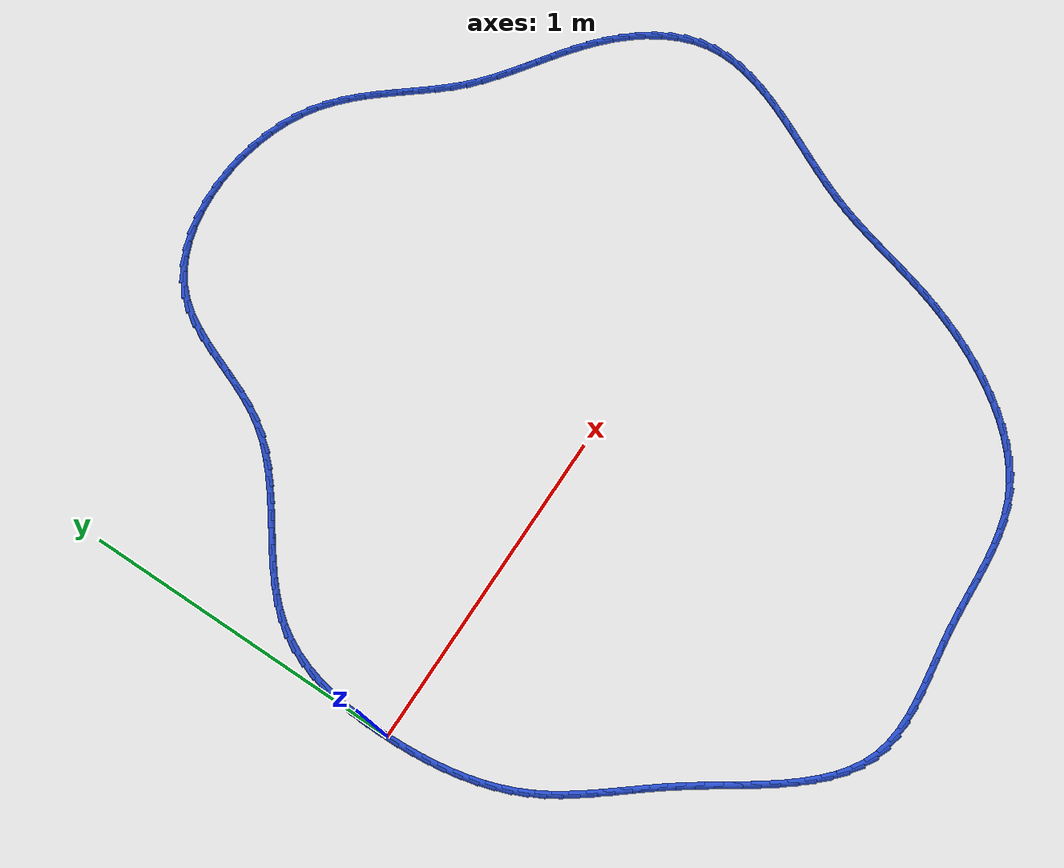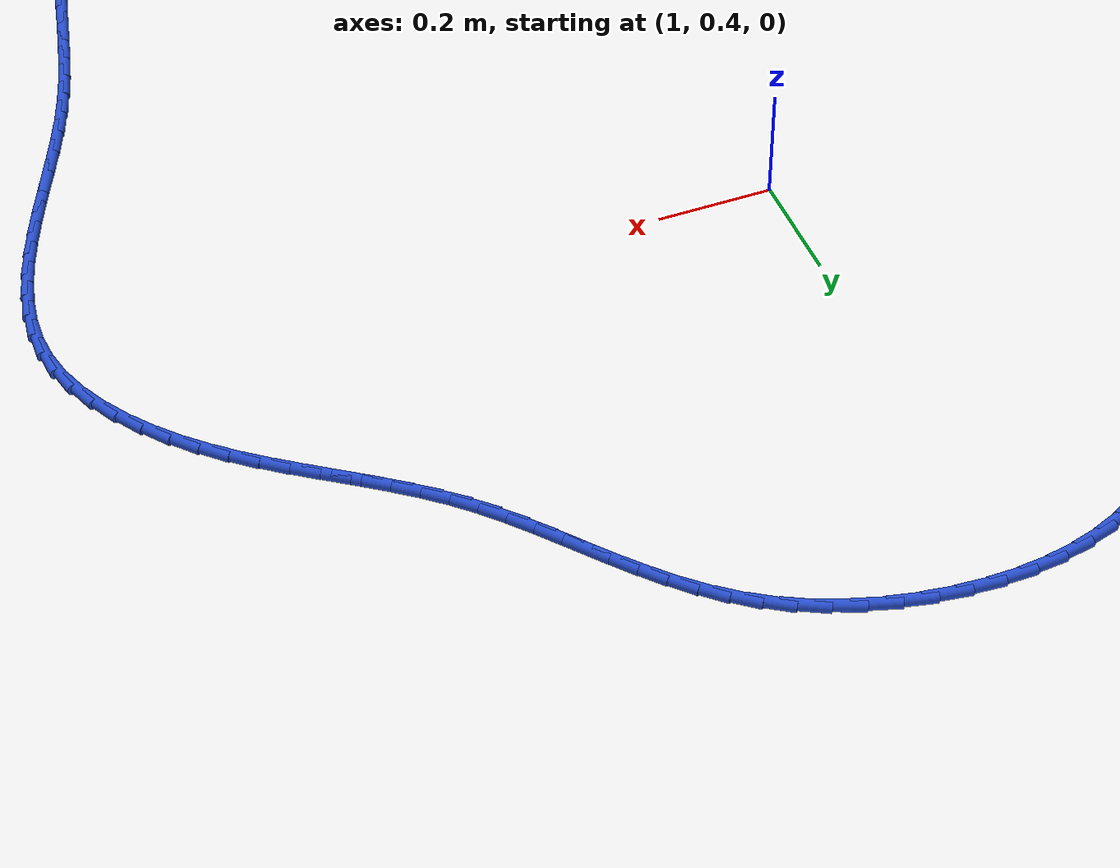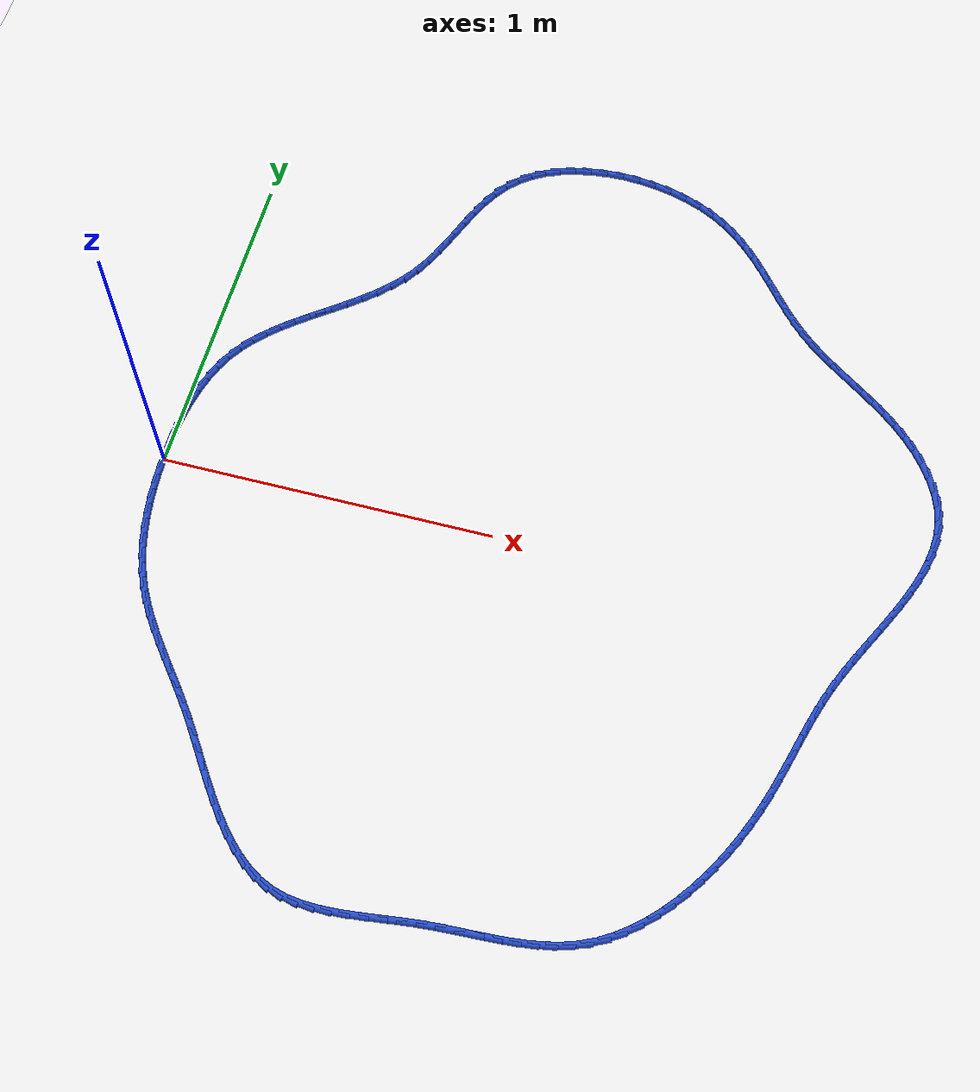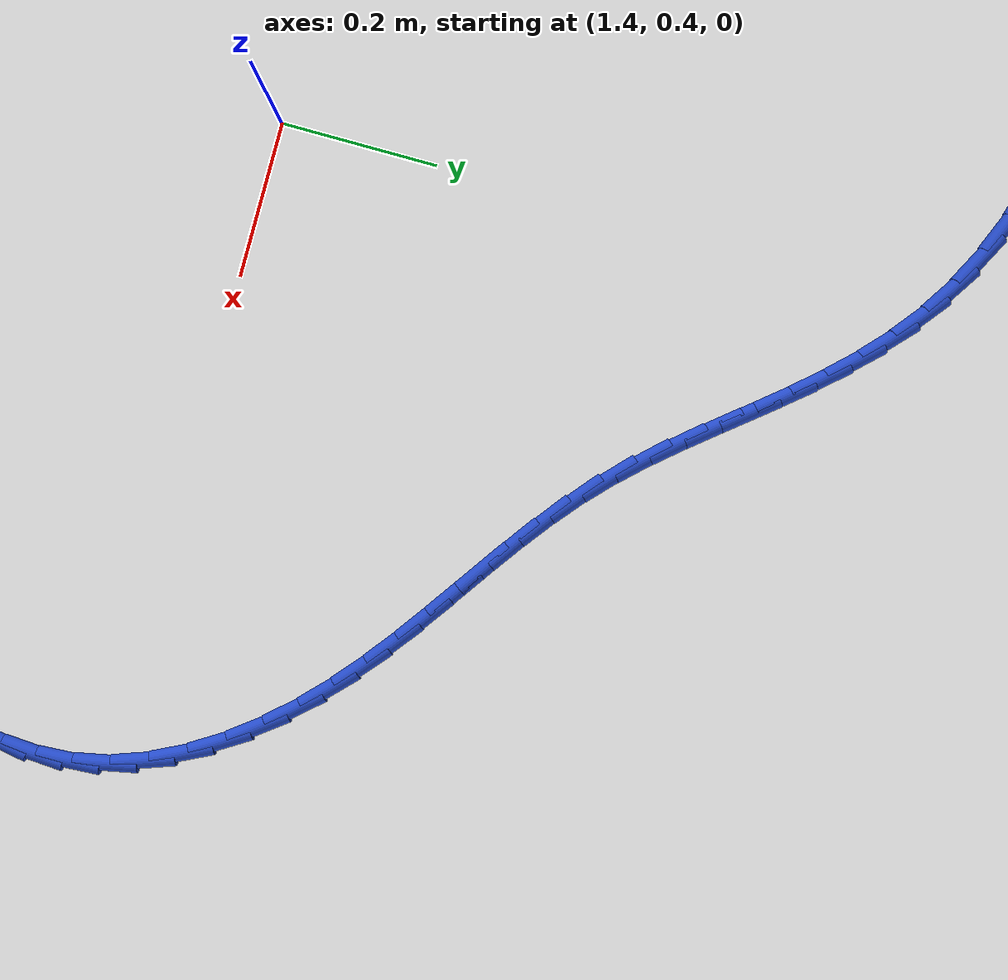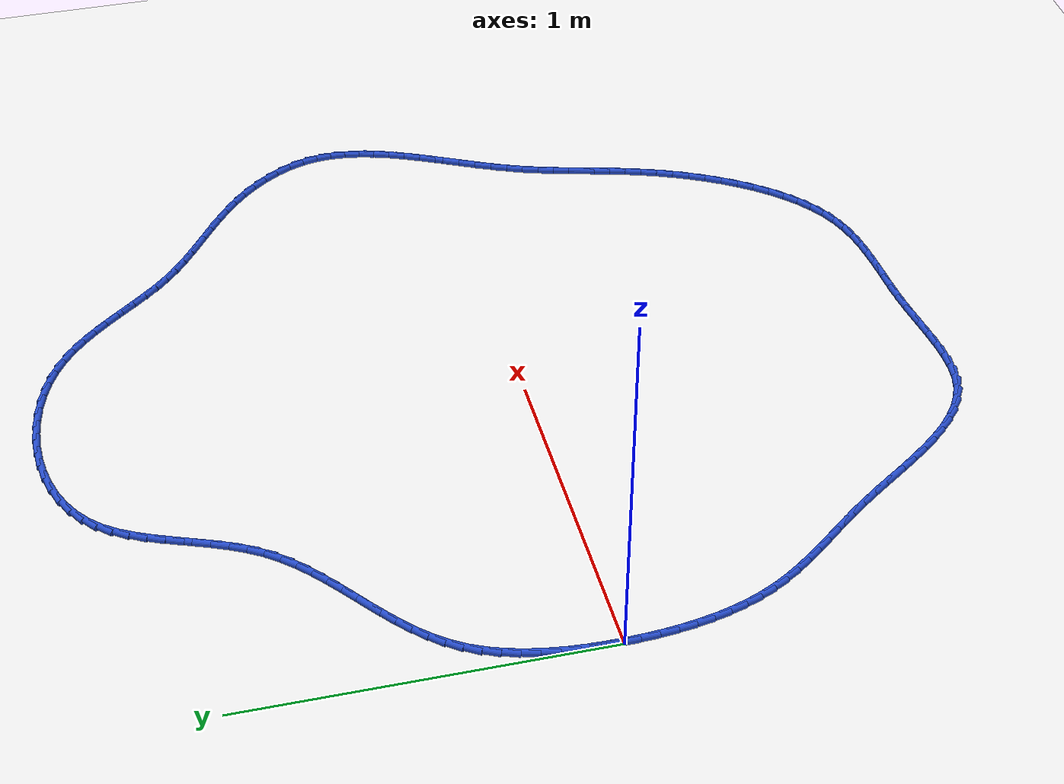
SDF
<sdf version="1.6">
 <world name="default">
  <light name="sun" type="directional">
   <pose>0 0 10 0 -0 0</pose>
   <diffuse>0.8 0.8 0.8 1</diffuse>
   <specular>0.2 0.2 0.2 1</specular>
   <attenuation>
    <range>1000</range>
    <constant>0.9</constant>
    <linear>0.01</linear>
    <quadratic>0.001</quadratic>
   </attenuation>
   <direction>-0.5 0.1 -0.9</direction>
  </light>
  <model name="ground_plane">
   <static>1</static>
   <link name="link">
    <collision name="collision">
     <geometry><plane><normal>0 0 1</normal><size>100 100</size></plane></geometry>
     <surface><friction><ode><mu>100</mu><mu2>50</mu2></ode></friction></surface>
    </collision>
    <visual name="visual">
     <cast_shadows>0</cast_shadows>
     <geometry><plane><normal>0 0 1</normal><size>100 100</size></plane></geometry>
     <material>
      <script><uri>file://media/materials/scripts/gazebo.material</uri><name>Gazebo/WhiteGlow</name></script>
     </material>
    </visual>
   </link>
  </model>
  <gravity>0 0 -9.8</gravity>
  <magnetic_field>6e-06 2.3e-05 -4.2e-05</magnetic_field>
  <atmosphere type="adiabatic"/>
  <physics name="default_physics" default="0" type="ode">
   <max_step_size>0.001</max_step_size>
   <real_time_factor>1</real_time_factor>
   <real_time_update_rate>1000</real_time_update_rate>
  </physics>
  <scene><ambient>0.4 0.4 0.4 1</ambient><background>0.7 0.7 0.7 1</background><shadows>1</shadows></scene>
  <spherical_coordinates>
   <surface_model>EARTH_WGS84</surface_model>
   <latitude_deg>0</latitude_deg>
   <longitude_deg>0</longitude_deg>
   <elevation>0</elevation>
   <heading_deg>0</heading_deg>
  </spherical_coordinates>
  <model name="line">
   <link name="link_0">
    <pose>3.903127820947816e-17 -9.71445146547012e-17 0.01 0 1.57 -1.5665078907945915</pose>
    <collision name="collision">
     <geometry><cylinder><radius>0.01</radius><length>0.08</length></cylinder></geometry>
    </collision>
    <visual name="visual">
     <material>
      <script><name>Gazebo/Blue</name><uri>file://media/materials/scripts/gazebo.material</uri></script>
     </material>
     <geometry><cylinder><radius>0.01</radius><length>0.08</length></cylinder></geometry>
    </visual>
   </link>
   <link name="link_1">
    <pose>-0.00021776998812928487 0.05078043676822143 0.01 0 1.57 1.5362645749410226</pose>
    <collision name="collision">
     <geometry><cylinder><radius>0.01</radius><length>0.08</length></cylinder></geometry>
    </collision>
    <visual name="visual">
     <material>
      <script><name>Gazebo/Blue</name><uri>file://media/materials/scripts/gazebo.material</uri></script>
     </material>
     <geometry><cylinder><radius>0.01</radius><length>0.08</length></cylinder></geometry>
    </visual>
   </link>
   <link name="link_2">
    <pose>0.0015339669497802014 0.10148856789524614 0.01 0 1.57 1.490337265067527</pose>
    <collision name="collision">
     <geometry><cylinder><radius>0.01</radius><length>0.08</length></cylinder></geometry>
    </collision>
    <visual name="visual">
     <material>
      <script><name>Gazebo/Blue</name><uri>file://media/materials/scripts/gazebo.material</uri></script>
     </material>
     <geometry><cylinder><radius>0.01</radius><length>0.08</length></cylinder></geometry>
    </visual>
   </link>
   <link name="link_3">
    <pose>0.00558555432442037 0.1517357450943004 0.01 0 1.57 1.4363469865343408</pose>
    <collision name="collision">
     <geometry><cylinder><radius>0.01</radius><length>0.08</length></cylinder></geometry>
    </collision>
    <visual name="visual">
     <material>
      <script><name>Gazebo/Blue</name><uri>file://media/materials/scripts/gazebo.material</uri></script>
     </material>
     <geometry><cylinder><radius>0.01</radius><length>0.08</length></cylinder></geometry>
    </visual>
   </link>
   <link name="link_4">
    <pose>0.012267335646483097 0.2011333200786106 0.01 0 1.57 1.37319205572349</pose>
    <collision name="collision">
     <geometry><cylinder><radius>0.01</radius><length>0.08</length></cylinder></geometry>
    </collision>
    <visual name="visual">
     <material>
      <script><name>Gazebo/Blue</name><uri>file://media/materials/scripts/gazebo.material</uri></script>
     </material>
     <geometry><cylinder><radius>0.01</radius><length>0.08</length></cylinder></geometry>
    </visual>
   </link>
   <link name="link_5">
    <pose>0.02190965442666025 0.24929264456140315 0.01 0 1.57 1.2996993328609765</pose>
    <collision name="collision">
     <geometry><cylinder><radius>0.01</radius><length>0.08</length></cylinder></geometry>
    </collision>
    <visual name="visual">
     <material>
      <script><name>Gazebo/Blue</name><uri>file://media/materials/scripts/gazebo.material</uri></script>
     </material>
     <geometry><cylinder><radius>0.01</radius><length>0.08</length></cylinder></geometry>
    </visual>
   </link>
   <link name="link_6">
    <pose>0.034842854175643714 0.2958250702559045 0.01 0 1.57 1.214773916480472</pose>
    <collision name="collision">
     <geometry><cylinder><radius>0.01</radius><length>0.08</length></cylinder></geometry>
    </collision>
    <visual name="visual">
     <material>
      <script><name>Gazebo/Blue</name><uri>file://media/materials/scripts/gazebo.material</uri></script>
     </material>
     <geometry><cylinder><radius>0.01</radius><length>0.08</length></cylinder></geometry>
    </visual>
   </link>
   <link name="link_7">
    <pose>0.05139727840412536 0.3403419488753411 0.01 0 1.57 1.1176580658109911</pose>
    <collision name="collision">
     <geometry><cylinder><radius>0.01</radius><length>0.08</length></cylinder></geometry>
    </collision>
    <visual name="visual">
     <material>
      <script><name>Gazebo/Blue</name><uri>file://media/materials/scripts/gazebo.material</uri></script>
     </material>
     <geometry><cylinder><radius>0.01</radius><length>0.08</length></cylinder></geometry>
    </visual>
   </link>
   <link name="link_8">
    <pose>0.07190327062279704 0.38245463213293907 0.01 0 1.57 1.0086001765209236</pose>
    <collision name="collision">
     <geometry><cylinder><radius>0.01</radius><length>0.08</length></cylinder></geometry>
    </collision>
    <visual name="visual">
     <material>
      <script><name>Gazebo/Blue</name><uri>file://media/materials/scripts/gazebo.material</uri></script>
     </material>
     <geometry><cylinder><radius>0.01</radius><length>0.08</length></cylinder></geometry>
    </visual>
   </link>
   <link name="link_9">
    <pose>0.09668090085959263 0.421783383661874 0.01 0 1.57 0.9006516839340023</pose>
    <collision name="collision">
     <geometry><cylinder><radius>0.01</radius><length>0.08</length></cylinder></geometry>
    </collision>
    <visual name="visual">
     <material>
      <script><name>Gazebo/Blue</name><uri>file://media/materials/scripts/gazebo.material</uri></script>
     </material>
     <geometry><cylinder><radius>0.01</radius><length>0.08</length></cylinder></geometry>
    </visual>
   </link>
   <link name="link_10">
    <pose>0.12563014930665417 0.4583128816834464 0.01 0 1.57 0.8114361110938803</pose>
    <collision name="collision">
     <geometry><cylinder><radius>0.01</radius><length>0.08</length></cylinder></geometry>
    </collision>
    <visual name="visual">
     <material>
      <script><name>Gazebo/Blue</name><uri>file://media/materials/scripts/gazebo.material</uri></script>
     </material>
     <geometry><cylinder><radius>0.01</radius><length>0.08</length></cylinder></geometry>
    </visual>
   </link>
   <link name="link_11">
    <pose>0.15809299289128564 0.4925118545258721 0.01 0 1.57 0.7424206700754056</pose>
    <collision name="collision">
     <geometry><cylinder><radius>0.01</radius><length>0.08</length></cylinder></geometry>
    </collision>
    <visual name="visual">
     <material>
      <script><name>Gazebo/Blue</name><uri>file://media/materials/scripts/gazebo.material</uri></script>
     </material>
     <geometry><cylinder><radius>0.01</radius><length>0.08</length></cylinder></geometry>
    </visual>
   </link>
   <link name="link_12">
    <pose>0.19337285360434386 0.5248824757000119 0.01 0 1.57 0.6928025710875316</pose>
    <collision name="collision">
     <geometry><cylinder><radius>0.01</radius><length>0.08</length></cylinder></geometry>
    </collision>
    <visual name="visual">
     <material>
      <script><name>Gazebo/Blue</name><uri>file://media/materials/scripts/gazebo.material</uri></script>
     </material>
     <geometry><cylinder><radius>0.01</radius><length>0.08</length></cylinder></geometry>
    </visual>
   </link>
   <link name="link_13">
    <pose>0.23077315343668575 0.5559269187167268 0.01 0 1.57 0.6614261168781185</pose>
    <collision name="collision">
     <geometry><cylinder><radius>0.01</radius><length>0.08</length></cylinder></geometry>
    </collision>
    <visual name="visual">
     <material>
      <script><name>Gazebo/Blue</name><uri>file://media/materials/scripts/gazebo.material</uri></script>
     </material>
     <geometry><cylinder><radius>0.01</radius><length>0.08</length></cylinder></geometry>
    </visual>
   </link>
   <link name="link_14">
    <pose>0.2695973143791681 0.5861473570868777 0.01 0 1.57 0.6472933082343424</pose>
    <collision name="collision">
     <geometry><cylinder><radius>0.01</radius><length>0.08</length></cylinder></geometry>
    </collision>
    <visual name="visual">
     <material>
      <script><name>Gazebo/Blue</name><uri>file://media/materials/scripts/gazebo.material</uri></script>
     </material>
     <geometry><cylinder><radius>0.01</radius><length>0.08</length></cylinder></geometry>
    </visual>
   </link>
   <link name="link_15">
    <pose>0.30914875842264783 0.6160459643213256 0.01 0 1.57 0.6498146580403017</pose>
    <collision name="collision">
     <geometry><cylinder><radius>0.01</radius><length>0.08</length></cylinder></geometry>
    </collision>
    <visual name="visual">
     <material>
      <script><name>Gazebo/Blue</name><uri>file://media/materials/scripts/gazebo.material</uri></script>
     </material>
     <geometry><cylinder><radius>0.01</radius><length>0.08</length></cylinder></geometry>
    </visual>
   </link>
   <link name="link_16">
    <pose>0.34873090755798186 0.6461249139309321 0.01 0 1.57 0.6688920855835448</pose>
    <collision name="collision">
     <geometry><cylinder><radius>0.01</radius><length>0.08</length></cylinder></geometry>
    </collision>
    <visual name="visual">
     <material>
      <script><name>Gazebo/Blue</name><uri>file://media/materials/scripts/gazebo.material</uri></script>
     </material>
     <geometry><cylinder><radius>0.01</radius><length>0.08</length></cylinder></geometry>
    </visual>
   </link>
   <link name="link_17">
    <pose>0.38764718377602714 0.6768863794265575 0.01 0 1.57 0.7048866489453667</pose>
    <collision name="collision">
     <geometry><cylinder><radius>0.01</radius><length>0.08</length></cylinder></geometry>
    </collision>
    <visual name="visual">
     <material>
      <script><name>Gazebo/Blue</name><uri>file://media/materials/scripts/gazebo.material</uri></script>
     </material>
     <geometry><cylinder><radius>0.01</radius><length>0.08</length></cylinder></geometry>
    </visual>
   </link>
   <link name="link_18">
    <pose>0.4252010090676404 0.708832534319063 0.01 0 1.57 0.7584722635348621</pose>
    <collision name="collision">
     <geometry><cylinder><radius>0.01</radius><length>0.08</length></cylinder></geometry>
    </collision>
    <visual name="visual">
     <material>
      <script><name>Gazebo/Blue</name><uri>file://media/materials/scripts/gazebo.material</uri></script>
     </material>
     <geometry><cylinder><radius>0.01</radius><length>0.08</length></cylinder></geometry>
    </visual>
   </link>
   <link name="link_19">
    <pose>0.46069580542367844 0.7424655521193093 0.01 0 1.57 0.8303330194741779</pose>
    <collision name="collision">
     <geometry><cylinder><radius>0.01</radius><length>0.08</length></cylinder></geometry>
    </collision>
    <visual name="visual">
     <material>
      <script><name>Gazebo/Blue</name><uri>file://media/materials/scripts/gazebo.material</uri></script>
     </material>
     <geometry><cylinder><radius>0.01</radius><length>0.08</length></cylinder></geometry>
    </visual>
   </link>
   <link name="link_20">
    <pose>0.4934349948349982 0.7782876063381576 0.01 0 1.57 0.920647395929913</pose>
    <collision name="collision">
     <geometry><cylinder><radius>0.01</radius><length>0.08</length></cylinder></geometry>
    </collision>
    <visual name="visual">
     <material>
      <script><name>Gazebo/Blue</name><uri>file://media/materials/scripts/gazebo.material</uri></script>
     </material>
     <geometry><cylinder><radius>0.01</radius><length>0.08</length></cylinder></geometry>
    </visual>
   </link>
   <link name="link_21">
    <pose>0.5227219992924568 0.8168008704864695 0.01 0 1.57 1.0240096917019041</pose>
    <collision name="collision">
     <geometry><cylinder><radius>0.01</radius><length>0.08</length></cylinder></geometry>
    </collision>
    <visual name="visual">
     <material>
      <script><name>Gazebo/Blue</name><uri>file://media/materials/scripts/gazebo.material</uri></script>
     </material>
     <geometry><cylinder><radius>0.01</radius><length>0.08</length></cylinder></geometry>
    </visual>
   </link>
   <link name="link_22">
    <pose>0.5480275524140348 0.8583744856599039 0.01 0 1.57 1.1099008937512582</pose>
    <collision name="collision">
     <geometry><cylinder><radius>0.01</radius><length>0.08</length></cylinder></geometry>
    </collision>
    <visual name="visual">
     <material>
      <script><name>Gazebo/Blue</name><uri>file://media/materials/scripts/gazebo.material</uri></script>
     </material>
     <geometry><cylinder><radius>0.01</radius><length>0.08</length></cylinder></geometry>
    </visual>
   </link>
   <link name="link_23">
    <pose>0.5699351493587663 0.902492816696223 0.01 0 1.57 1.167297756255069</pose>
    <collision name="collision">
     <geometry><cylinder><radius>0.01</radius><length>0.08</length></cylinder></geometry>
    </collision>
    <visual name="visual">
     <material>
      <script><name>Gazebo/Blue</name><uri>file://media/materials/scripts/gazebo.material</uri></script>
     </material>
     <geometry><cylinder><radius>0.01</radius><length>0.08</length></cylinder></geometry>
    </visual>
   </link>
   <link name="link_24">
    <pose>0.5894824025876251 0.9482791517853757 0.01 0 1.57 1.197803876333992</pose>
    <collision name="collision">
     <geometry><cylinder><radius>0.01</radius><length>0.08</length></cylinder></geometry>
    </collision>
    <visual name="visual">
     <material>
      <script><name>Gazebo/Blue</name><uri>file://media/materials/scripts/gazebo.material</uri></script>
     </material>
     <geometry><cylinder><radius>0.01</radius><length>0.08</length></cylinder></geometry>
    </visual>
   </link>
   <link name="link_25">
    <pose>0.6077082669741406 0.9948557117414983 0.01 0 1.57 1.2024416871880363</pose>
    <collision name="collision">
     <geometry><cylinder><radius>0.01</radius><length>0.08</length></cylinder></geometry>
    </collision>
    <visual name="visual">
     <material>
      <script><name>Gazebo/Blue</name><uri>file://media/materials/scripts/gazebo.material</uri></script>
     </material>
     <geometry><cylinder><radius>0.01</radius><length>0.08</length></cylinder></geometry>
    </visual>
   </link>
   <link name="link_26">
    <pose>0.6256516973918413 1.0413447173787254 0.01 0 1.57 1.1810364653430174</pose>
    <collision name="collision">
     <geometry><cylinder><radius>0.01</radius><length>0.08</length></cylinder></geometry>
    </collision>
    <visual name="visual">
     <material>
      <script><name>Gazebo/Blue</name><uri>file://media/materials/scripts/gazebo.material</uri></script>
     </material>
     <geometry><cylinder><radius>0.01</radius><length>0.08</length></cylinder></geometry>
    </visual>
   </link>
   <link name="link_27">
    <pose>0.6443516487142568 1.086868389511191 0.01 0 1.57 1.132081352651135</pose>
    <collision name="collision">
     <geometry><cylinder><radius>0.01</radius><length>0.08</length></cylinder></geometry>
    </collision>
    <visual name="visual">
     <material>
      <script><name>Gazebo/Blue</name><uri>file://media/materials/scripts/gazebo.material</uri></script>
     </material>
     <geometry><cylinder><radius>0.01</radius><length>0.08</length></cylinder></geometry>
    </visual>
   </link>
   <link name="link_28">
    <pose>0.6648470758149156 1.1305489489530314 0.01 0 1.57 1.0530439334400847</pose>
    <collision name="collision">
     <geometry><cylinder><radius>0.01</radius><length>0.08</length></cylinder></geometry>
    </collision>
    <visual name="visual">
     <material>
      <script><name>Gazebo/Blue</name><uri>file://media/materials/scripts/gazebo.material</uri></script>
     </material>
     <geometry><cylinder><radius>0.01</radius><length>0.08</length></cylinder></geometry>
    </visual>
   </link>
   <link name="link_29">
    <pose>0.6881769335673472 1.1715086165183806 0.01 0 1.57 0.9414468973535122</pose>
    <collision name="collision">
     <geometry><cylinder><radius>0.01</radius><length>0.08</length></cylinder></geometry>
    </collision>
    <visual name="visual">
     <material>
      <script><name>Gazebo/Blue</name><uri>file://media/materials/scripts/gazebo.material</uri></script>
     </material>
     <geometry><cylinder><radius>0.01</radius><length>0.08</length></cylinder></geometry>
    </visual>
   </link>
   <link name="link_30">
    <pose>0.7153801768450802 1.2088696130213732 0.01 0 1.57 0.7979616281621175</pose>
    <collision name="collision">
     <geometry><cylinder><radius>0.01</radius><length>0.08</length></cylinder></geometry>
    </collision>
    <visual name="visual">
     <material>
      <script><name>Gazebo/Blue</name><uri>file://media/materials/scripts/gazebo.material</uri></script>
     </material>
     <geometry><cylinder><radius>0.01</radius><length>0.08</length></cylinder></geometry>
    </visual>
   </link>
   <link name="link_31">
    <pose>0.7474653323309163 1.241771271007985 0.01 0 1.57 0.6459846368756833</pose>
    <collision name="collision">
     <geometry><cylinder><radius>0.01</radius><length>0.08</length></cylinder></geometry>
    </collision>
    <visual name="visual">
     <material>
      <script><name>Gazebo/Blue</name><uri>file://media/materials/scripts/gazebo.material</uri></script>
     </material>
     <geometry><cylinder><radius>0.01</radius><length>0.08</length></cylinder></geometry>
    </visual>
   </link>
   <link name="link_32">
    <pose>0.7846449668918919 1.269800542504592 0.01 0 1.57 0.5088235489701044</pose>
    <collision name="collision">
     <geometry><cylinder><radius>0.01</radius><length>0.08</length></cylinder></geometry>
    </collision>
    <visual name="visual">
     <material>
      <script><name>Gazebo/Blue</name><uri>file://media/materials/scripts/gazebo.material</uri></script>
     </material>
     <geometry><cylinder><radius>0.01</radius><length>0.08</length></cylinder></geometry>
    </visual>
   </link>
   <link name="link_33">
    <pose>0.8262783211273758 1.2930242598694421 0.01 0 1.57 0.3870737006810017</pose>
    <collision name="collision">
     <geometry><cylinder><radius>0.01</radius><length>0.08</length></cylinder></geometry>
    </collision>
    <visual name="visual">
     <material>
      <script><name>Gazebo/Blue</name><uri>file://media/materials/scripts/gazebo.material</uri></script>
     </material>
     <geometry><cylinder><radius>0.01</radius><length>0.08</length></cylinder></geometry>
    </visual>
   </link>
   <link name="link_34">
    <pose>0.8716827167334245 1.3115328291605468 0.01 0 1.57 0.2788477642974198</pose>
    <collision name="collision">
     <geometry><cylinder><radius>0.01</radius><length>0.08</length></cylinder></geometry>
    </collision>
    <visual name="visual">
     <material>
      <script><name>Gazebo/Blue</name><uri>file://media/materials/scripts/gazebo.material</uri></script>
     </material>
     <geometry><cylinder><radius>0.01</radius><length>0.08</length></cylinder></geometry>
    </visual>
   </link>
   <link name="link_35">
    <pose>0.9201754754060937 1.325416656435915 0.01 0 1.57 0.18166398945779935</pose>
    <collision name="collision">
     <geometry><cylinder><radius>0.01</radius><length>0.08</length></cylinder></geometry>
    </collision>
    <visual name="visual">
     <material>
      <script><name>Gazebo/Blue</name><uri>file://media/materials/scripts/gazebo.material</uri></script>
     </material>
     <geometry><cylinder><radius>0.01</radius><length>0.08</length></cylinder></geometry>
    </visual>
   </link>
   <link name="link_36">
    <pose>0.97107391884144 1.3347661477535584 0.01 0 1.57 0.09295494987377644</pose>
    <collision name="collision">
     <geometry><cylinder><radius>0.01</radius><length>0.08</length></cylinder></geometry>
    </collision>
    <visual name="visual">
     <material>
      <script><name>Gazebo/Blue</name><uri>file://media/materials/scripts/gazebo.material</uri></script>
     </material>
     <geometry><cylinder><radius>0.01</radius><length>0.08</length></cylinder></geometry>
    </visual>
   </link>
   <link name="link_37">
    <pose>1.023695368735519 1.3396717091714867 0.01 0 1.57 0.010286988682800771</pose>
    <collision name="collision">
     <geometry><cylinder><radius>0.01</radius><length>0.08</length></cylinder></geometry>
    </collision>
    <visual name="visual">
     <material>
      <script><name>Gazebo/Blue</name><uri>file://media/materials/scripts/gazebo.material</uri></script>
     </material>
     <geometry><cylinder><radius>0.01</radius><length>0.08</length></cylinder></geometry>
    </visual>
   </link>
   <link name="link_38">
    <pose>1.0773571467843877 1.3402237467477103 0.01 0 1.57 -0.06859122017718487</pose>
    <collision name="collision">
     <geometry><cylinder><radius>0.01</radius><length>0.08</length></cylinder></geometry>
    </collision>
    <visual name="visual">
     <material>
      <script><name>Gazebo/Blue</name><uri>file://media/materials/scripts/gazebo.material</uri></script>
     </material>
     <geometry><cylinder><radius>0.01</radius><length>0.08</length></cylinder></geometry>
    </visual>
   </link>
   <link name="link_39">
    <pose>1.1313765746841016 1.3365126665402398 0.01 0 1.57 -0.14578541319424707</pose>
    <collision name="collision">
     <geometry><cylinder><radius>0.01</radius><length>0.08</length></cylinder></geometry>
    </collision>
    <visual name="visual">
     <material>
      <script><name>Gazebo/Blue</name><uri>file://media/materials/scripts/gazebo.material</uri></script>
     </material>
     <geometry><cylinder><radius>0.01</radius><length>0.08</length></cylinder></geometry>
    </visual>
   </link>
   <link name="link_40">
    <pose>1.1850709741307175 1.328628874607086 0.01 0 1.57 -0.2233294925358326</pose>
    <collision name="collision">
     <geometry><cylinder><radius>0.01</radius><length>0.08</length></cylinder></geometry>
    </collision>
    <visual name="visual">
     <material>
      <script><name>Gazebo/Blue</name><uri>file://media/materials/scripts/gazebo.material</uri></script>
     </material>
     <geometry><cylinder><radius>0.01</radius><length>0.08</length></cylinder></geometry>
    </visual>
   </link>
   <link name="link_41">
    <pose>1.2377576668202912 1.316662777006259 0.01 0 1.57 -0.3032716108715075</pose>
    <collision name="collision">
     <geometry><cylinder><radius>0.01</radius><length>0.08</length></cylinder></geometry>
    </collision>
    <visual name="visual">
     <material>
      <script><name>Gazebo/Blue</name><uri>file://media/materials/scripts/gazebo.material</uri></script>
     </material>
     <geometry><cylinder><radius>0.01</radius><length>0.08</length></cylinder></geometry>
    </visual>
   </link>
   <link name="link_42">
    <pose>1.2887539744488787 1.3007047797957694 0.01 0 1.57 -0.3877576998434893</pose>
    <collision name="collision">
     <geometry><cylinder><radius>0.01</radius><length>0.08</length></cylinder></geometry>
    </collision>
    <visual name="visual">
     <material>
      <script><name>Gazebo/Blue</name><uri>file://media/materials/scripts/gazebo.material</uri></script>
     </material>
     <geometry><cylinder><radius>0.01</radius><length>0.08</length></cylinder></geometry>
    </visual>
   </link>
   <link name="link_43">
    <pose>1.3373772187125366 1.2808452890336273 0.01 0 1.57 -0.47909557566976546</pose>
    <collision name="collision">
     <geometry><cylinder><radius>0.01</radius><length>0.08</length></cylinder></geometry>
    </collision>
    <visual name="visual">
     <material>
      <script><name>Gazebo/Blue</name><uri>file://media/materials/scripts/gazebo.material</uri></script>
     </material>
     <geometry><cylinder><radius>0.01</radius><length>0.08</length></cylinder></geometry>
    </visual>
   </link>
   <link name="link_44">
    <pose>1.382944721307321 1.2571747107778435 0.01 0 1.57 -0.5778630486349271</pose>
    <collision name="collision">
     <geometry><cylinder><radius>0.01</radius><length>0.08</length></cylinder></geometry>
    </collision>
    <visual name="visual">
     <material>
      <script><name>Gazebo/Blue</name><uri>file://media/materials/scripts/gazebo.material</uri></script>
     </material>
     <geometry><cylinder><radius>0.01</radius><length>0.08</length></cylinder></geometry>
    </visual>
   </link>
   <link name="link_45">
    <pose>1.4248817046867637 1.22982682868086 0.01 0 1.57 -0.670587735578084</pose>
    <collision name="collision">
     <geometry><cylinder><radius>0.01</radius><length>0.08</length></cylinder></geometry>
    </collision>
    <visual name="visual">
     <material>
      <script><name>Gazebo/Blue</name><uri>file://media/materials/scripts/gazebo.material</uri></script>
     </material>
     <geometry><cylinder><radius>0.01</radius><length>0.08</length></cylinder></geometry>
    </visual>
   </link>
   <link name="link_46">
    <pose>1.463418431041542 1.1992590634856821 0.01 0 1.57 -0.7484623457011957</pose>
    <collision name="collision">
     <geometry><cylinder><radius>0.01</radius><length>0.08</length></cylinder></geometry>
    </collision>
    <visual name="visual">
     <material>
      <script><name>Gazebo/Blue</name><uri>file://media/materials/scripts/gazebo.material</uri></script>
     </material>
     <geometry><cylinder><radius>0.01</radius><length>0.08</length></cylinder></geometry>
    </visual>
   </link>
   <link name="link_47">
    <pose>1.4991489735888635 1.166075092991594 0.01 0 1.57 -0.8097773036211393</pose>
    <collision name="collision">
     <geometry><cylinder><radius>0.01</radius><length>0.08</length></cylinder></geometry>
    </collision>
    <visual name="visual">
     <material>
      <script><name>Gazebo/Blue</name><uri>file://media/materials/scripts/gazebo.material</uri></script>
     </material>
     <geometry><cylinder><radius>0.01</radius><length>0.08</length></cylinder></geometry>
    </visual>
   </link>
   <link name="link_48">
    <pose>1.5326691866914544 1.130879311042972 0.01 0 1.57 -0.8538581449817241</pose>
    <collision name="collision">
     <geometry><cylinder><radius>0.01</radius><length>0.08</length></cylinder></geometry>
    </collision>
    <visual name="visual">
     <material>
      <script><name>Gazebo/Blue</name><uri>file://media/materials/scripts/gazebo.material</uri></script>
     </material>
     <geometry><cylinder><radius>0.01</radius><length>0.08</length></cylinder></geometry>
    </visual>
   </link>
   <link name="link_49">
    <pose>1.5645749247120395 1.0942761114841926 0.01 0 1.57 -0.8805672174371061</pose>
    <collision name="collision">
     <geometry><cylinder><radius>0.01</radius><length>0.08</length></cylinder></geometry>
    </collision>
    <visual name="visual">
     <material>
      <script><name>Gazebo/Blue</name><uri>file://media/materials/scripts/gazebo.material</uri></script>
     </material>
     <geometry><cylinder><radius>0.01</radius><length>0.08</length></cylinder></geometry>
    </visual>
   </link>
   <link name="link_50">
    <pose>1.5954620420133467 1.056869888159632 0.01 0 1.57 -0.889916532141338</pose>
    <collision name="collision">
     <geometry><cylinder><radius>0.01</radius><length>0.08</length></cylinder></geometry>
    </collision>
    <visual name="visual">
     <material>
      <script><name>Gazebo/Blue</name><uri>file://media/materials/scripts/gazebo.material</uri></script>
     </material>
     <geometry><cylinder><radius>0.01</radius><length>0.08</length></cylinder></geometry>
    </visual>
   </link>
   <link name="link_51">
    <pose>1.625926392958101 1.0192650349136676 0.01 0 1.57 -0.8818255697473878</pose>
    <collision name="collision">
     <geometry><cylinder><radius>0.01</radius><length>0.08</length></cylinder></geometry>
    </collision>
    <visual name="visual">
     <material>
      <script><name>Gazebo/Blue</name><uri>file://media/materials/scripts/gazebo.material</uri></script>
     </material>
     <geometry><cylinder><radius>0.01</radius><length>0.08</length></cylinder></geometry>
    </visual>
   </link>
   <link name="link_52">
    <pose>1.6565638319090277 0.9820659455906747 0.01 0 1.57 -0.8560331456970506</pose>
    <collision name="collision">
     <geometry><cylinder><radius>0.01</radius><length>0.08</length></cylinder></geometry>
    </collision>
    <visual name="visual">
     <material>
      <script><name>Gazebo/Blue</name><uri>file://media/materials/scripts/gazebo.material</uri></script>
     </material>
     <geometry><cylinder><radius>0.01</radius><length>0.08</length></cylinder></geometry>
    </visual>
   </link>
   <link name="link_53">
    <pose>1.6879702132288534 0.9458770140350308 0.01 0 1.57 -0.8121671324895129</pose>
    <collision name="collision">
     <geometry><cylinder><radius>0.01</radius><length>0.08</length></cylinder></geometry>
    </collision>
    <visual name="visual">
     <material>
      <script><name>Gazebo/Blue</name><uri>file://media/materials/scripts/gazebo.material</uri></script>
     </material>
     <geometry><cylinder><radius>0.01</radius><length>0.08</length></cylinder></geometry>
    </visual>
   </link>
   <link name="link_54">
    <pose>1.720741391280304 0.9113026340911117 0.01 0 1.57 -0.7513501178696858</pose>
    <collision name="collision">
     <geometry><cylinder><radius>0.01</radius><length>0.08</length></cylinder></geometry>
    </collision>
    <visual name="visual">
     <material>
      <script><name>Gazebo/Blue</name><uri>file://media/materials/scripts/gazebo.material</uri></script>
     </material>
     <geometry><cylinder><radius>0.01</radius><length>0.08</length></cylinder></geometry>
    </visual>
   </link>
   <link name="link_55">
    <pose>1.755430449444342 0.8788988395766576 0.01 0 1.57 -0.6922541889673912</pose>
    <collision name="collision">
     <geometry><cylinder><radius>0.01</radius><length>0.08</length></cylinder></geometry>
    </collision>
    <visual name="visual">
     <material>
      <script><name>Gazebo/Blue</name><uri>file://media/materials/scripts/gazebo.material</uri></script>
     </material>
     <geometry><cylinder><radius>0.01</radius><length>0.08</length></cylinder></geometry>
    </visual>
   </link>
   <link name="link_56">
    <pose>1.7920121384225778 0.8485677587261015 0.01 0 1.57 -0.6485488712155655</pose>
    <collision name="collision">
     <geometry><cylinder><radius>0.01</radius><length>0.08</length></cylinder></geometry>
    </collision>
    <visual name="visual">
     <material>
      <script><name>Gazebo/Blue</name><uri>file://media/materials/scripts/gazebo.material</uri></script>
     </material>
     <geometry><cylinder><radius>0.01</radius><length>0.08</length></cylinder></geometry>
    </visual>
   </link>
   <link name="link_57">
    <pose>1.8300455700944407 0.8197415678652843 0.01 0 1.57 -0.6205406093908845</pose>
    <collision name="collision">
     <geometry><cylinder><radius>0.01</radius><length>0.08</length></cylinder></geometry>
    </collision>
    <visual name="visual">
     <material>
      <script><name>Gazebo/Blue</name><uri>file://media/materials/scripts/gazebo.material</uri></script>
     </material>
     <geometry><cylinder><radius>0.01</radius><length>0.08</length></cylinder></geometry>
    </visual>
   </link>
   <link name="link_58">
    <pose>1.8690807412601105 0.7918421371391454 0.01 0 1.57 -0.6080076414258095</pose>
    <collision name="collision">
     <geometry><cylinder><radius>0.01</radius><length>0.08</length></cylinder></geometry>
    </collision>
    <visual name="visual">
     <material>
      <script><name>Gazebo/Blue</name><uri>file://media/materials/scripts/gazebo.material</uri></script>
     </material>
     <geometry><cylinder><radius>0.01</radius><length>0.08</length></cylinder></geometry>
    </visual>
   </link>
   <link name="link_59">
    <pose>1.908667648719765 0.7642913366926253 0.01 0 1.57 -0.6106963986476253</pose>
    <collision name="collision">
     <geometry><cylinder><radius>0.01</radius><length>0.08</length></cylinder></geometry>
    </collision>
    <visual name="visual">
     <material>
      <script><name>Gazebo/Blue</name><uri>file://media/materials/scripts/gazebo.material</uri></script>
     </material>
     <geometry><cylinder><radius>0.01</radius><length>0.08</length></cylinder></geometry>
    </visual>
   </link>
   <link name="link_60">
    <pose>1.9483562892735833 0.7365110366706634 0.01 0 1.57 -0.6284096501497202</pose>
    <collision name="collision">
     <geometry><cylinder><radius>0.01</radius><length>0.08</length></cylinder></geometry>
    </collision>
    <visual name="visual">
     <material>
      <script><name>Gazebo/Blue</name><uri>file://media/materials/scripts/gazebo.material</uri></script>
     </material>
     <geometry><cylinder><radius>0.01</radius><length>0.08</length></cylinder></geometry>
    </visual>
   </link>
   <link name="link_61">
    <pose>1.9876966597217443 0.7079231072181997 0.01 0 1.57 -0.6609866183630148</pose>
    <collision name="collision">
     <geometry><cylinder><radius>0.01</radius><length>0.08</length></cylinder></geometry>
    </collision>
    <visual name="visual">
     <material>
      <script><name>Gazebo/Blue</name><uri>file://media/materials/scripts/gazebo.material</uri></script>
     </material>
     <geometry><cylinder><radius>0.01</radius><length>0.08</length></cylinder></geometry>
    </visual>
   </link>
   <link name="link_62">
    <pose>2.026238756864427 0.6779494184801739 0.01 0 1.57 -0.7081847291299853</pose>
    <collision name="collision">
     <geometry><cylinder><radius>0.01</radius><length>0.08</length></cylinder></geometry>
    </collision>
    <visual name="visual">
     <material>
      <script><name>Gazebo/Blue</name><uri>file://media/materials/scripts/gazebo.material</uri></script>
     </material>
     <geometry><cylinder><radius>0.01</radius><length>0.08</length></cylinder></geometry>
    </visual>
   </link>
   <link name="link_63">
    <pose>2.063532577501809 0.6460118406015259 0.01 0 1.57 -0.7694734384676561</pose>
    <collision name="collision">
     <geometry><cylinder><radius>0.01</radius><length>0.08</length></cylinder></geometry>
    </collision>
    <visual name="visual">
     <material>
      <script><name>Gazebo/Blue</name><uri>file://media/materials/scripts/gazebo.material</uri></script>
     </material>
     <geometry><cylinder><radius>0.01</radius><length>0.08</length></cylinder></geometry>
    </visual>
   </link>
   <link name="link_64">
    <pose>2.0991280664604703 0.6115323704326537 0.01 0 1.57 -0.8421143319772979</pose>
    <collision name="collision">
     <geometry><cylinder><radius>0.01</radius><length>0.08</length></cylinder></geometry>
    </collision>
    <visual name="visual">
     <material>
      <script><name>Gazebo/Blue</name><uri>file://media/materials/scripts/gazebo.material</uri></script>
     </material>
     <geometry><cylinder><radius>0.01</radius><length>0.08</length></cylinder></geometry>
    </visual>
   </link>
   <link name="link_65">
    <pose>2.1324798478708185 0.5741653853495192 0.01 0 1.57 -0.9216232566486755</pose>
    <collision name="collision">
     <geometry><cylinder><radius>0.01</radius><length>0.08</length></cylinder></geometry>
    </collision>
    <visual name="visual">
     <material>
      <script><name>Gazebo/Blue</name><uri>file://media/materials/scripts/gazebo.material</uri></script>
     </material>
     <geometry><cylinder><radius>0.01</radius><length>0.08</length></cylinder></geometry>
    </visual>
   </link>
   <link name="link_66">
    <pose>2.1627499349139905 0.5342786134368767 0.01 0 1.57 -1.0103895304095358</pose>
    <collision name="collision">
     <geometry><cylinder><radius>0.01</radius><length>0.08</length></cylinder></geometry>
    </collision>
    <visual name="visual">
     <material>
      <script><name>Gazebo/Blue</name><uri>file://media/materials/scripts/gazebo.material</uri></script>
     </material>
     <geometry><cylinder><radius>0.01</radius><length>0.08</length></cylinder></geometry>
    </visual>
   </link>
   <link name="link_67">
    <pose>2.189044379774215 0.49237620903732104 0.01 0 1.57 -1.1123603026348177</pose>
    <collision name="collision">
     <geometry><cylinder><radius>0.01</radius><length>0.08</length></cylinder></geometry>
    </collision>
    <visual name="visual">
     <material>
      <script><name>Gazebo/Blue</name><uri>file://media/materials/scripts/gazebo.material</uri></script>
     </material>
     <geometry><cylinder><radius>0.01</radius><length>0.08</length></cylinder></geometry>
    </visual>
   </link>
   <link name="link_68">
    <pose>2.210469234635718 0.4489623264934487 0.01 0 1.57 -1.2318391719254351</pose>
    <collision name="collision">
     <geometry><cylinder><radius>0.01</radius><length>0.08</length></cylinder></geometry>
    </collision>
    <visual name="visual">
     <material>
      <script><name>Gazebo/Blue</name><uri>file://media/materials/scripts/gazebo.material</uri></script>
     </material>
     <geometry><cylinder><radius>0.01</radius><length>0.08</length></cylinder></geometry>
    </visual>
   </link>
   <link name="link_69">
    <pose>2.226130551682727 0.40454112014785476 0.01 0 1.57 -1.371380939646697</pose>
    <collision name="collision">
     <geometry><cylinder><radius>0.01</radius><length>0.08</length></cylinder></geometry>
    </collision>
    <visual name="visual">
     <material>
      <script><name>Gazebo/Blue</name><uri>file://media/materials/scripts/gazebo.material</uri></script>
     </material>
     <geometry><cylinder><radius>0.01</radius><length>0.08</length></cylinder></geometry>
    </visual>
   </link>
   <link name="link_70">
    <pose>2.235214508949604 0.35959361348533037 0.01 0 1.57 -1.5128867403425124</pose>
    <collision name="collision">
     <geometry><cylinder><radius>0.01</radius><length>0.08</length></cylinder></geometry>
    </collision>
    <visual name="visual">
     <material>
      <script><name>Gazebo/Blue</name><uri>file://media/materials/scripts/gazebo.material</uri></script>
     </material>
     <geometry><cylinder><radius>0.01</radius><length>0.08</length></cylinder></geometry>
    </visual>
   </link>
   <link name="link_71">
    <pose>2.2378385242578944 0.3143319982083829 0.01 0 1.57 1.502435199325925</pose>
    <collision name="collision">
     <geometry><cylinder><radius>0.01</radius><length>0.08</length></cylinder></geometry>
    </collision>
    <visual name="visual">
     <material>
      <script><name>Gazebo/Blue</name><uri>file://media/materials/scripts/gazebo.material</uri></script>
     </material>
     <geometry><cylinder><radius>0.01</radius><length>0.08</length></cylinder></geometry>
    </visual>
   </link>
   <link name="link_72">
    <pose>2.234720709315024 0.26879505675353993 0.01 0 1.57 1.3949942508130686</pose>
    <collision name="collision">
     <geometry><cylinder><radius>0.01</radius><length>0.08</length></cylinder></geometry>
    </collision>
    <visual name="visual">
     <material>
      <script><name>Gazebo/Blue</name><uri>file://media/materials/scripts/gazebo.material</uri></script>
     </material>
     <geometry><cylinder><radius>0.01</radius><length>0.08</length></cylinder></geometry>
    </visual>
   </link>
   <link name="link_73">
    <pose>2.226589182632983 0.22301868277707718 0.01 0 1.57 1.307032935243157</pose>
    <collision name="collision">
     <geometry><cylinder><radius>0.01</radius><length>0.08</length></cylinder></geometry>
    </collision>
    <visual name="visual">
     <material>
      <script><name>Gazebo/Blue</name><uri>file://media/materials/scripts/gazebo.material</uri></script>
     </material>
     <geometry><cylinder><radius>0.01</radius><length>0.08</length></cylinder></geometry>
    </visual>
   </link>
   <link name="link_74">
    <pose>2.214172062723761 0.17703876993527046 0.01 0 1.57 1.2375435129487957</pose>
    <collision name="collision">
     <geometry><cylinder><radius>0.01</radius><length>0.08</length></cylinder></geometry>
    </collision>
    <visual name="visual">
     <material>
      <script><name>Gazebo/Blue</name><uri>file://media/materials/scripts/gazebo.material</uri></script>
     </material>
     <geometry><cylinder><radius>0.01</radius><length>0.08</length></cylinder></geometry>
    </visual>
   </link>
   <link name="link_75">
    <pose>2.198197468099347 0.130891211884396 0.01 0 1.57 1.1848583645781385</pose>
    <collision name="collision">
     <geometry><cylinder><radius>0.01</radius><length>0.08</length></cylinder></geometry>
    </collision>
    <visual name="visual">
     <material>
      <script><name>Gazebo/Blue</name><uri>file://media/materials/scripts/gazebo.material</uri></script>
     </material>
     <geometry><cylinder><radius>0.01</radius><length>0.08</length></cylinder></geometry>
    </visual>
   </link>
   <link name="link_76">
    <pose>2.1793935172717305 0.08461190228072943 0.01 0 1.57 1.147290527098107</pose>
    <collision name="collision">
     <geometry><cylinder><radius>0.01</radius><length>0.08</length></cylinder></geometry>
    </collision>
    <visual name="visual">
     <material>
      <script><name>Gazebo/Blue</name><uri>file://media/materials/scripts/gazebo.material</uri></script>
     </material>
     <geometry><cylinder><radius>0.01</radius><length>0.08</length></cylinder></geometry>
    </visual>
   </link>
   <link name="link_77">
    <pose>2.158488328752901 0.038236734780547114 0.01 0 1.57 1.1234611192526023</pose>
    <collision name="collision">
     <geometry><cylinder><radius>0.01</radius><length>0.08</length></cylinder></geometry>
    </collision>
    <visual name="visual">
     <material>
      <script><name>Gazebo/Blue</name><uri>file://media/materials/scripts/gazebo.material</uri></script>
     </material>
     <geometry><cylinder><radius>0.01</radius><length>0.08</length></cylinder></geometry>
    </visual>
   </link>
   <link name="link_78">
    <pose>2.13621002105485 -0.008198396959874066 0.01 0 1.57 1.112436794668999</pose>
    <collision name="collision">
     <geometry><cylinder><radius>0.01</radius><length>0.08</length></cylinder></geometry>
    </collision>
    <visual name="visual">
     <material>
      <script><name>Gazebo/Blue</name><uri>file://media/materials/scripts/gazebo.material</uri></script>
     </material>
     <geometry><cylinder><radius>0.01</radius><length>0.08</length></cylinder></geometry>
    </visual>
   </link>
   <link name="link_79">
    <pose>2.1132867126895647 -0.05465759928425971 0.01 0 1.57 1.113775816945982</pose>
    <collision name="collision">
     <geometry><cylinder><radius>0.01</radius><length>0.08</length></cylinder></geometry>
    </collision>
    <visual name="visual">
     <material>
      <script><name>Gazebo/Blue</name><uri>file://media/materials/scripts/gazebo.material</uri></script>
     </material>
     <geometry><cylinder><radius>0.01</radius><length>0.08</length></cylinder></geometry>
    </visual>
   </link>
   <link name="link_80">
    <pose>2.0904465221690356 -0.10110497853633217 0.01 0 1.57 1.1275394233834508</pose>
    <collision name="collision">
     <geometry><cylinder><radius>0.01</radius><length>0.08</length></cylinder></geometry>
    </collision>
    <visual name="visual">
     <material>
      <script><name>Gazebo/Blue</name><uri>file://media/materials/scripts/gazebo.material</uri></script>
     </material>
     <geometry><cylinder><radius>0.01</radius><length>0.08</length></cylinder></geometry>
    </visual>
   </link>
   <link name="link_81">
    <pose>2.0684175680052523 -0.14750464105981695 0.01 0 1.57 1.1542917428528983</pose>
    <collision name="collision">
     <geometry><cylinder><radius>0.01</radius><length>0.08</length></cylinder></geometry>
    </collision>
    <visual name="visual">
     <material>
      <script><name>Gazebo/Blue</name><uri>file://media/materials/scripts/gazebo.material</uri></script>
     </material>
     <geometry><cylinder><radius>0.01</radius><length>0.08</length></cylinder></geometry>
    </visual>
   </link>
   <link name="link_82">
    <pose>2.047927968710204 -0.19382069319843728 0.01 0 1.57 1.1945491460301552</pose>
    <collision name="collision">
     <geometry><cylinder><radius>0.01</radius><length>0.08</length></cylinder></geometry>
    </collision>
    <visual name="visual">
     <material>
      <script><name>Gazebo/Blue</name><uri>file://media/materials/scripts/gazebo.material</uri></script>
     </material>
     <geometry><cylinder><radius>0.01</radius><length>0.08</length></cylinder></geometry>
    </visual>
   </link>
   <link name="link_83">
    <pose>2.0296764123890405 -0.24001924617836637 0.01 0 1.57 1.237798065656722</pose>
    <collision name="collision">
     <geometry><cylinder><radius>0.01</radius><length>0.08</length></cylinder></geometry>
    </collision>
    <visual name="visual">
     <material>
      <script><name>Gazebo/Blue</name><uri>file://media/materials/scripts/gazebo.material</uri></script>
     </material>
     <geometry><cylinder><radius>0.01</radius><length>0.08</length></cylinder></geometry>
    </visual>
   </link>
   <link name="link_84">
    <pose>2.013734929550565 -0.2861091009114472 0.01 0 1.57 1.2723767447680818</pose>
    <collision name="collision">
     <geometry><cylinder><radius>0.01</radius><length>0.08</length></cylinder></geometry>
    </collision>
    <visual name="visual">
     <material>
      <script><name>Gazebo/Blue</name><uri>file://media/materials/scripts/gazebo.material</uri></script>
     </material>
     <geometry><cylinder><radius>0.01</radius><length>0.08</length></cylinder></geometry>
    </visual>
   </link>
   <link name="link_85">
    <pose>1.9995755960874382 -0.33213992891274446 0.01 0 1.57 1.2969270239284647</pose>
    <collision name="collision">
     <geometry><cylinder><radius>0.01</radius><length>0.08</length></cylinder></geometry>
    </collision>
    <visual name="visual">
     <material>
      <script><name>Gazebo/Blue</name><uri>file://media/materials/scripts/gazebo.material</uri></script>
     </material>
     <geometry><cylinder><radius>0.01</radius><length>0.08</length></cylinder></geometry>
    </visual>
   </link>
   <link name="link_86">
    <pose>1.9866464012564198 -0.3781630425470042 0.01 0 1.57 1.310870744472133</pose>
    <collision name="collision">
     <geometry><cylinder><radius>0.01</radius><length>0.08</length></cylinder></geometry>
    </collision>
    <visual name="visual">
     <material>
      <script><name>Gazebo/Blue</name><uri>file://media/materials/scripts/gazebo.material</uri></script>
     </material>
     <geometry><cylinder><radius>0.01</radius><length>0.08</length></cylinder></geometry>
    </visual>
   </link>
   <link name="link_87">
    <pose>1.9743953343142704 -0.42422975417896974 0.01 0 1.57 1.313935516654081</pose>
    <collision name="collision">
     <geometry><cylinder><radius>0.01</radius><length>0.08</length></cylinder></geometry>
    </collision>
    <visual name="visual">
     <material>
      <script><name>Gazebo/Blue</name><uri>file://media/materials/scripts/gazebo.material</uri></script>
     </material>
     <geometry><cylinder><radius>0.01</radius><length>0.08</length></cylinder></geometry>
    </visual>
   </link>
   <link name="link_88">
    <pose>1.9622703845177525 -0.47039137617338506 0.01 0 1.57 1.3061241584045669</pose>
    <collision name="collision">
     <geometry><cylinder><radius>0.01</radius><length>0.08</length></cylinder></geometry>
    </collision>
    <visual name="visual">
     <material>
      <script><name>Gazebo/Blue</name><uri>file://media/materials/scripts/gazebo.material</uri></script>
     </material>
     <geometry><cylinder><radius>0.01</radius><length>0.08</length></cylinder></geometry>
    </visual>
   </link>
   <link name="link_89">
    <pose>1.9497195411236254 -0.5166992208949959 0.01 0 1.57 1.2877023263319503</pose>
    <collision name="collision">
     <geometry><cylinder><radius>0.01</radius><length>0.08</length></cylinder></geometry>
    </collision>
    <visual name="visual">
     <material>
      <script><name>Gazebo/Blue</name><uri>file://media/materials/scripts/gazebo.material</uri></script>
     </material>
     <geometry><cylinder><radius>0.01</radius><length>0.08</length></cylinder></geometry>
    </visual>
   </link>
   <link name="link_90">
    <pose>1.9361907933886517 -0.5632046007085457 0.01 0 1.57 1.2592065426602248</pose>
    <collision name="collision">
     <geometry><cylinder><radius>0.01</radius><length>0.08</length></cylinder></geometry>
    </collision>
    <visual name="visual">
     <material>
      <script><name>Gazebo/Blue</name><uri>file://media/materials/scripts/gazebo.material</uri></script>
     </material>
     <geometry><cylinder><radius>0.01</radius><length>0.08</length></cylinder></geometry>
    </visual>
   </link>
   <link name="link_91">
    <pose>1.9211321305695923 -0.6099588279787783 0.01 0 1.57 1.2219186392631105</pose>
    <collision name="collision">
     <geometry><cylinder><radius>0.01</radius><length>0.08</length></cylinder></geometry>
    </collision>
    <visual name="visual">
     <material>
      <script><name>Gazebo/Blue</name><uri>file://media/materials/scripts/gazebo.material</uri></script>
     </material>
     <geometry><cylinder><radius>0.01</radius><length>0.08</length></cylinder></geometry>
    </visual>
   </link>
   <link name="link_92">
    <pose>1.9040258923885005 -0.656985361331058 0.01 0 1.57 1.1810063561791417</pose>
    <collision name="collision">
     <geometry><cylinder><radius>0.01</radius><length>0.08</length></cylinder></geometry>
    </collision>
    <visual name="visual">
     <material>
      <script><name>Gazebo/Blue</name><uri>file://media/materials/scripts/gazebo.material</uri></script>
     </material>
     <geometry><cylinder><radius>0.01</radius><length>0.08</length></cylinder></geometry>
    </visual>
   </link>
   <link name="link_93">
    <pose>1.8847008460181476 -0.7040267519897903 0.01 0 1.57 1.1385644556251986</pose>
    <collision name="collision">
     <geometry><cylinder><radius>0.01</radius><length>0.08</length></cylinder></geometry>
    </collision>
    <visual name="visual">
     <material>
      <script><name>Gazebo/Blue</name><uri>file://media/materials/scripts/gazebo.material</uri></script>
     </material>
     <geometry><cylinder><radius>0.01</radius><length>0.08</length></cylinder></geometry>
    </visual>
   </link>
   <link name="link_94">
    <pose>1.863186463786932 -0.750662805520779 0.01 0 1.57 1.093834689427655</pose>
    <collision name="collision">
     <geometry><cylinder><radius>0.01</radius><length>0.08</length></cylinder></geometry>
    </collision>
    <visual name="visual">
     <material>
      <script><name>Gazebo/Blue</name><uri>file://media/materials/scripts/gazebo.material</uri></script>
     </material>
     <geometry><cylinder><radius>0.01</radius><length>0.08</length></cylinder></geometry>
    </visual>
   </link>
   <link name="link_95">
    <pose>1.8395146734349448 -0.796471336471751 0.01 0 1.57 1.0459995892679423</pose>
    <collision name="collision">
     <geometry><cylinder><radius>0.01</radius><length>0.08</length></cylinder></geometry>
    </collision>
    <visual name="visual">
     <material>
      <script><name>Gazebo/Blue</name><uri>file://media/materials/scripts/gazebo.material</uri></script>
     </material>
     <geometry><cylinder><radius>0.01</radius><length>0.08</length></cylinder></geometry>
    </visual>
   </link>
   <link name="link_96">
    <pose>1.813717402702276 -0.8410301593904312 0.01 0 1.57 0.9941864259702774</pose>
    <collision name="collision">
     <geometry><cylinder><radius>0.01</radius><length>0.08</length></cylinder></geometry>
    </collision>
    <visual name="visual">
     <material>
      <script><name>Gazebo/Blue</name><uri>file://media/materials/scripts/gazebo.material</uri></script>
     </material>
     <geometry><cylinder><radius>0.01</radius><length>0.08</length></cylinder></geometry>
    </visual>
   </link>
   <link name="link_97">
    <pose>1.785826579329015 -0.8839170888245487 0.01 0 1.57 0.9374469109844183</pose>
    <collision name="collision">
     <geometry><cylinder><radius>0.01</radius><length>0.08</length></cylinder></geometry>
    </collision>
    <visual name="visual">
     <material>
      <script><name>Gazebo/Blue</name><uri>file://media/materials/scripts/gazebo.material</uri></script>
     </material>
     <geometry><cylinder><radius>0.01</radius><length>0.08</length></cylinder></geometry>
    </visual>
   </link>
   <link name="link_98">
    <pose>1.755874131055251 -0.9247099393218283 0.01 0 1.57 0.8747490651686205</pose>
    <collision name="collision">
     <geometry><cylinder><radius>0.01</radius><length>0.08</length></cylinder></geometry>
    </collision>
    <visual name="visual">
     <material>
      <script><name>Gazebo/Blue</name><uri>file://media/materials/scripts/gazebo.material</uri></script>
     </material>
     <geometry><cylinder><radius>0.01</radius><length>0.08</length></cylinder></geometry>
    </visual>
   </link>
   <link name="link_99">
    <pose>1.7238919856210746 -0.9629865254299985 0.01 0 1.57 0.8049897071748252</pose>
    <collision name="collision">
     <geometry><cylinder><radius>0.01</radius><length>0.08</length></cylinder></geometry>
    </collision>
    <visual name="visual">
     <material>
      <script><name>Gazebo/Blue</name><uri>file://media/materials/scripts/gazebo.material</uri></script>
     </material>
     <geometry><cylinder><radius>0.01</radius><length>0.08</length></cylinder></geometry>
    </visual>
   </link>
   <link name="link_100">
    <pose>1.6899120707665753 -0.9983246616967851 0.01 0 1.57 0.7270418638243707</pose>
    <collision name="collision">
     <geometry><cylinder><radius>0.01</radius><length>0.08</length></cylinder></geometry>
    </collision>
    <visual name="visual">
     <material>
      <script><name>Gazebo/Blue</name><uri>file://media/materials/scripts/gazebo.material</uri></script>
     </material>
     <geometry><cylinder><radius>0.01</radius><length>0.08</length></cylinder></geometry>
    </visual>
   </link>
   <link name="link_101">
    <pose>1.6539663142318444 -1.0303021626699145 0.01 0 1.57 0.6398574121040104</pose>
    <collision name="collision">
     <geometry><cylinder><radius>0.01</radius><length>0.08</length></cylinder></geometry>
    </collision>
    <visual name="visual">
     <material>
      <script><name>Gazebo/Blue</name><uri>file://media/materials/scripts/gazebo.material</uri></script>
     </material>
     <geometry><cylinder><radius>0.01</radius><length>0.08</length></cylinder></geometry>
    </visual>
   </link>
   <link name="link_102">
    <pose>1.6160866437569699 -1.0584968428971144 0.01 0 1.57 0.5426470738250866</pose>
    <collision name="collision">
     <geometry><cylinder><radius>0.01</radius><length>0.08</length></cylinder></geometry>
    </collision>
    <visual name="visual">
     <material>
      <script><name>Gazebo/Blue</name><uri>file://media/materials/scripts/gazebo.material</uri></script>
     </material>
     <geometry><cylinder><radius>0.01</radius><length>0.08</length></cylinder></geometry>
    </visual>
   </link>
   <link name="link_103">
    <pose>1.5763049870820425 -1.0824865169261113 0.01 0 1.57 0.43520589727855974</pose>
    <collision name="collision">
     <geometry><cylinder><radius>0.01</radius><length>0.08</length></cylinder></geometry>
    </collision>
    <visual name="visual">
     <material>
      <script><name>Gazebo/Blue</name><uri>file://media/materials/scripts/gazebo.material</uri></script>
     </material>
     <geometry><cylinder><radius>0.01</radius><length>0.08</length></cylinder></geometry>
    </visual>
   </link>
   <link name="link_104">
    <pose>1.5346536283179564 -1.1018517759970756 0.01 0 1.57 0.32613111817889523</pose>
    <collision name="collision">
     <geometry><cylinder><radius>0.01</radius><length>0.08</length></cylinder></geometry>
    </collision>
    <visual name="visual">
     <material>
      <script><name>Gazebo/Blue</name><uri>file://media/materials/scripts/gazebo.material</uri></script>
     </material>
     <geometry><cylinder><radius>0.01</radius><length>0.08</length></cylinder></geometry>
    </visual>
   </link>
   <link name="link_105">
    <pose>1.4912124305502454 -1.1165439268463355 0.01 0 1.57 0.23336789422450266</pose>
    <collision name="collision">
     <geometry><cylinder><radius>0.01</radius><length>0.08</length></cylinder></geometry>
    </collision>
    <visual name="visual">
     <material>
      <script><name>Gazebo/Blue</name><uri>file://media/materials/scripts/gazebo.material</uri></script>
     </material>
     <geometry><cylinder><radius>0.01</radius><length>0.08</length></cylinder></geometry>
    </visual>
   </link>
   <link name="link_106">
    <pose>1.446156162805757 -1.1272537436616976 0.01 0 1.57 0.16008862207527763</pose>
    <collision name="collision">
     <geometry><cylinder><radius>0.01</radius><length>0.08</length></cylinder></geometry>
    </collision>
    <visual name="visual">
     <material>
      <script><name>Gazebo/Blue</name><uri>file://media/materials/scripts/gazebo.material</uri></script>
     </material>
     <geometry><cylinder><radius>0.01</radius><length>0.08</length></cylinder></geometry>
    </visual>
   </link>
   <link name="link_107">
    <pose>1.3996708554739707 -1.1347597444646211 0.01 0 1.57 0.10605111599772638</pose>
    <collision name="collision">
     <geometry><cylinder><radius>0.01</radius><length>0.08</length></cylinder></geometry>
    </collision>
    <visual name="visual">
     <material>
      <script><name>Gazebo/Blue</name><uri>file://media/materials/scripts/gazebo.material</uri></script>
     </material>
     <geometry><cylinder><radius>0.01</radius><length>0.08</length></cylinder></geometry>
    </visual>
   </link>
   <link name="link_108">
    <pose>1.3519425389443682 -1.1398404472765646 0.01 0 1.57 0.07027257805158596</pose>
    <collision name="collision">
     <geometry><cylinder><radius>0.01</radius><length>0.08</length></cylinder></geometry>
    </collision>
    <visual name="visual">
     <material>
      <script><name>Gazebo/Blue</name><uri>file://media/materials/scripts/gazebo.material</uri></script>
     </material>
     <geometry><cylinder><radius>0.01</radius><length>0.08</length></cylinder></geometry>
    </visual>
   </link>
   <link name="link_109">
    <pose>1.3031572436064291 -1.143274370118987 0.01 0 1.57 0.05162253989207205</pose>
    <collision name="collision">
     <geometry><cylinder><radius>0.01</radius><length>0.08</length></cylinder></geometry>
    </collision>
    <visual name="visual">
     <material>
      <script><name>Gazebo/Blue</name><uri>file://media/materials/scripts/gazebo.material</uri></script>
     </material>
     <geometry><cylinder><radius>0.01</radius><length>0.08</length></cylinder></geometry>
    </visual>
   </link>
   <link name="link_110">
    <pose>1.253500999849633 -1.1458400310133459 0.01 0 1.57 0.049143154525525964</pose>
    <collision name="collision">
     <geometry><cylinder><radius>0.01</radius><length>0.08</length></cylinder></geometry>
    </collision>
    <visual name="visual">
     <material>
      <script><name>Gazebo/Blue</name><uri>file://media/materials/scripts/gazebo.material</uri></script>
     </material>
     <geometry><cylinder><radius>0.01</radius><length>0.08</length></cylinder></geometry>
    </visual>
   </link>
   <link name="link_111">
    <pose>1.2031598380634616 -1.148315947981101 0.01 0 1.57 0.0621677800622184</pose>
    <collision name="collision">
     <geometry><cylinder><radius>0.01</radius><length>0.08</length></cylinder></geometry>
    </collision>
    <visual name="visual">
     <material>
      <script><name>Gazebo/Blue</name><uri>file://media/materials/scripts/gazebo.material</uri></script>
     </material>
     <geometry><cylinder><radius>0.01</radius><length>0.08</length></cylinder></geometry>
    </visual>
   </link>
   <link name="link_112">
    <pose>1.1523197886373961 -1.1514806390437105 0.01 0 1.57 0.09002186008904417</pose>
    <collision name="collision">
     <geometry><cylinder><radius>0.01</radius><length>0.08</length></cylinder></geometry>
    </collision>
    <visual name="visual">
     <material>
      <script><name>Gazebo/Blue</name><uri>file://media/materials/scripts/gazebo.material</uri></script>
     </material>
     <geometry><cylinder><radius>0.01</radius><length>0.08</length></cylinder></geometry>
    </visual>
   </link>
   <link name="link_113">
    <pose>1.1011680888002466 -1.1560978895866783 0.01 0 1.57 0.11906756375685604</pose>
    <collision name="collision">
     <geometry><cylinder><radius>0.01</radius><length>0.08</length></cylinder></geometry>
    </collision>
    <visual name="visual">
     <material>
      <script><name>Gazebo/Blue</name><uri>file://media/materials/scripts/gazebo.material</uri></script>
     </material>
     <geometry><cylinder><radius>0.01</radius><length>0.08</length></cylinder></geometry>
    </visual>
   </link>
   <link name="link_114">
    <pose>1.0499498230578168 -1.162225307420507 0.01 0 1.57 0.13058110718384763</pose>
    <collision name="collision">
     <geometry><cylinder><radius>0.01</radius><length>0.08</length></cylinder></geometry>
    </collision>
    <visual name="visual">
     <material>
      <script><name>Gazebo/Blue</name><uri>file://media/materials/scripts/gazebo.material</uri></script>
     </material>
     <geometry><cylinder><radius>0.01</radius><length>0.08</length></cylinder></geometry>
    </visual>
   </link>
   <link name="link_115">
    <pose>0.9989922389265684 -1.1689174855442113 0.01 0 1.57 0.12317605533995923</pose>
    <collision name="collision">
     <geometry><cylinder><radius>0.01</radius><length>0.08</length></cylinder></geometry>
    </collision>
    <visual name="visual">
     <material>
      <script><name>Gazebo/Blue</name><uri>file://media/materials/scripts/gazebo.material</uri></script>
     </material>
     <geometry><cylinder><radius>0.01</radius><length>0.08</length></cylinder></geometry>
    </visual>
   </link>
   <link name="link_116">
    <pose>0.9486288424002532 -1.1751526158443675 0.01 0 1.57 0.09591609672744952</pose>
    <collision name="collision">
     <geometry><cylinder><radius>0.01</radius><length>0.08</length></cylinder></geometry>
    </collision>
    <visual name="visual">
     <material>
      <script><name>Gazebo/Blue</name><uri>file://media/materials/scripts/gazebo.material</uri></script>
     </material>
     <geometry><cylinder><radius>0.01</radius><length>0.08</length></cylinder></geometry>
    </visual>
   </link>
   <link name="link_117">
    <pose>0.899193139472622 -1.1799088902075512 0.01 0 1.57 0.04678749173663298</pose>
    <collision name="collision">
     <geometry><cylinder><radius>0.01</radius><length>0.08</length></cylinder></geometry>
    </collision>
    <visual name="visual">
     <material>
      <script><name>Gazebo/Blue</name><uri>file://media/materials/scripts/gazebo.material</uri></script>
     </material>
     <geometry><cylinder><radius>0.01</radius><length>0.08</length></cylinder></geometry>
    </visual>
   </link>
   <link name="link_118">
    <pose>0.8510186361374239 -1.1821645005203372 0.01 0 1.57 -0.02719096430996269</pose>
    <collision name="collision">
     <geometry><cylinder><radius>0.01</radius><length>0.08</length></cylinder></geometry>
    </collision>
    <visual name="visual">
     <material>
      <script><name>Gazebo/Blue</name><uri>file://media/materials/scripts/gazebo.material</uri></script>
     </material>
     <geometry><cylinder><radius>0.01</radius><length>0.08</length></cylinder></geometry>
    </visual>
   </link>
   <link name="link_119">
    <pose>0.8044388383884109 -1.1808976386693015 0.01 0 1.57 -0.12941674257628674</pose>
    <collision name="collision">
     <geometry><cylinder><radius>0.01</radius><length>0.08</length></cylinder></geometry>
    </collision>
    <visual name="visual">
     <material>
      <script><name>Gazebo/Blue</name><uri>file://media/materials/scripts/gazebo.material</uri></script>
     </material>
     <geometry><cylinder><radius>0.01</radius><length>0.08</length></cylinder></geometry>
    </visual>
   </link>
   <link name="link_120">
    <pose>0.7597872522193323 -1.1750864965410202 0.01 0 1.57 -0.26215805260979347</pose>
    <collision name="collision">
     <geometry><cylinder><radius>0.01</radius><length>0.08</length></cylinder></geometry>
    </collision>
    <visual name="visual">
     <material>
      <script><name>Gazebo/Blue</name><uri>file://media/materials/scripts/gazebo.material</uri></script>
     </material>
     <geometry><cylinder><radius>0.01</radius><length>0.08</length></cylinder></geometry>
    </visual>
   </link>
   <link name="link_121">
    <pose>0.7173965393607145 -1.1637116420378675 0.01 0 1.57 -0.41218297625623423</pose>
    <collision name="collision">
     <geometry><cylinder><radius>0.01</radius><length>0.08</length></cylinder></geometry>
    </collision>
    <visual name="visual">
     <material>
      <script><name>Gazebo/Blue</name><uri>file://media/materials/scripts/gazebo.material</uri></script>
     </material>
     <geometry><cylinder><radius>0.01</radius><length>0.08</length></cylinder></geometry>
    </visual>
   </link>
   <link name="link_122">
    <pose>0.677427898639434 -1.1462361922913642 0.01 0 1.57 -0.5479385559670195</pose>
    <collision name="collision">
     <geometry><cylinder><radius>0.01</radius><length>0.08</length></cylinder></geometry>
    </collision>
    <visual name="visual">
     <material>
      <script><name>Gazebo/Blue</name><uri>file://media/materials/scripts/gazebo.material</uri></script>
     </material>
     <geometry><cylinder><radius>0.01</radius><length>0.08</length></cylinder></geometry>
    </visual>
   </link>
   <link name="link_123">
    <pose>0.6396636015948199 -1.1231896821047995 0.01 0 1.57 -0.6624117836331482</pose>
    <collision name="collision">
     <geometry><cylinder><radius>0.01</radius><length>0.08</length></cylinder></geometry>
    </collision>
    <visual name="visual">
     <material>
      <script><name>Gazebo/Blue</name><uri>file://media/materials/scripts/gazebo.material</uri></script>
     </material>
     <geometry><cylinder><radius>0.01</radius><length>0.08</length></cylinder></geometry>
    </visual>
   </link>
   <link name="link_124">
    <pose>0.6038352061893792 -1.0952443698495535 0.01 0 1.57 -0.755420773059732</pose>
    <collision name="collision">
     <geometry><cylinder><radius>0.01</radius><length>0.08</length></cylinder></geometry>
    </collision>
    <visual name="visual">
     <material>
      <script><name>Gazebo/Blue</name><uri>file://media/materials/scripts/gazebo.material</uri></script>
     </material>
     <geometry><cylinder><radius>0.01</radius><length>0.08</length></cylinder></geometry>
    </visual>
   </link>
   <link name="link_125">
    <pose>0.5696742703856189 -1.063072513897007 0.01 0 1.57 -0.8286520421434223</pose>
    <collision name="collision">
     <geometry><cylinder><radius>0.01</radius><length>0.08</length></cylinder></geometry>
    </collision>
    <visual name="visual">
     <material>
      <script><name>Gazebo/Blue</name><uri>file://media/materials/scripts/gazebo.material</uri></script>
     </material>
     <geometry><cylinder><radius>0.01</radius><length>0.08</length></cylinder></geometry>
    </visual>
   </link>
   <link name="link_126">
    <pose>0.5369123521460438 -1.027346372618538 0.01 0 1.57 -0.8844024878372101</pose>
    <collision name="collision">
     <geometry><cylinder><radius>0.01</radius><length>0.08</length></cylinder></geometry>
    </collision>
    <visual name="visual">
     <material>
      <script><name>Gazebo/Blue</name><uri>file://media/materials/scripts/gazebo.material</uri></script>
     </material>
     <geometry><cylinder><radius>0.01</radius><length>0.08</length></cylinder></geometry>
    </visual>
   </link>
   <link name="link_127">
    <pose>0.5052810094331616 -0.9887382043855273 0.01 0 1.57 -0.9248575204671827</pose>
    <collision name="collision">
     <geometry><cylinder><radius>0.01</radius><length>0.08</length></cylinder></geometry>
    </collision>
    <visual name="visual">
     <material>
      <script><name>Gazebo/Blue</name><uri>file://media/materials/scripts/gazebo.material</uri></script>
     </material>
     <geometry><cylinder><radius>0.01</radius><length>0.08</length></cylinder></geometry>
    </visual>
   </link>
   <link name="link_128">
    <pose>0.474511800209477 -0.9479202675693534 0.01 0 1.57 -0.9517731539576132</pose>
    <collision name="collision">
     <geometry><cylinder><radius>0.01</radius><length>0.08</length></cylinder></geometry>
    </collision>
    <visual name="visual">
     <material>
      <script><name>Gazebo/Blue</name><uri>file://media/materials/scripts/gazebo.material</uri></script>
     </material>
     <geometry><cylinder><radius>0.01</radius><length>0.08</length></cylinder></geometry>
    </visual>
   </link>
   <link name="link_129">
    <pose>0.4443362824374967 -0.9055648205413964 0.01 0 1.57 -0.9663748138506109</pose>
    <collision name="collision">
     <geometry><cylinder><radius>0.01</radius><length>0.08</length></cylinder></geometry>
    </collision>
    <visual name="visual">
     <material>
      <script><name>Gazebo/Blue</name><uri>file://media/materials/scripts/gazebo.material</uri></script>
     </material>
     <geometry><cylinder><radius>0.01</radius><length>0.08</length></cylinder></geometry>
    </visual>
   </link>
   <link name="link_130">
    <pose>0.4144860140797278 -0.8623441216730368 0.01 0 1.57 -0.9693455260705565</pose>
    <collision name="collision">
     <geometry><cylinder><radius>0.01</radius><length>0.08</length></cylinder></geometry>
    </collision>
    <visual name="visual">
     <material>
      <script><name>Gazebo/Blue</name><uri>file://media/materials/scripts/gazebo.material</uri></script>
     </material>
     <geometry><cylinder><radius>0.01</radius><length>0.08</length></cylinder></geometry>
    </visual>
   </link>
   <link name="link_131">
    <pose>0.3846925530986753 -0.8189304293356527 0.01 0 1.57 -0.9608367854623902</pose>
    <collision name="collision">
     <geometry><cylinder><radius>0.01</radius><length>0.08</length></cylinder></geometry>
    </collision>
    <visual name="visual">
     <material>
      <script><name>Gazebo/Blue</name><uri>file://media/materials/scripts/gazebo.material</uri></script>
     </material>
     <geometry><cylinder><radius>0.01</radius><length>0.08</length></cylinder></geometry>
    </visual>
   </link>
   <link name="link_132">
    <pose>0.35468745745684627 -0.775996001900625 0.01 0 1.57 -0.9405130359087103</pose>
    <collision name="collision">
     <geometry><cylinder><radius>0.01</radius><length>0.08</length></cylinder></geometry>
    </collision>
    <visual name="visual">
     <material>
      <script><name>Gazebo/Blue</name><uri>file://media/materials/scripts/gazebo.material</uri></script>
     </material>
     <geometry><cylinder><radius>0.01</radius><length>0.08</length></cylinder></geometry>
    </visual>
   </link>
   <link name="link_133">
    <pose>0.32420346312883036 -0.7342112739880076 0.01 0 1.57 -0.9144335182135365</pose>
    <collision name="collision">
     <geometry><cylinder><radius>0.01</radius><length>0.08</length></cylinder></geometry>
    </collision>
    <visual name="visual">
     <material>
      <script><name>Gazebo/Blue</name><uri>file://media/materials/scripts/gazebo.material</uri></script>
     </material>
     <geometry><cylinder><radius>0.01</radius><length>0.08</length></cylinder></geometry>
    </visual>
   </link>
   <link name="link_134">
    <pose>0.2931765861131411 -0.6939319701924701 0.01 0 1.57 -0.8971356732714064</pose>
    <collision name="collision">
     <geometry><cylinder><radius>0.01</radius><length>0.08</length></cylinder></geometry>
    </collision>
    <visual name="visual">
     <material>
      <script><name>Gazebo/Blue</name><uri>file://media/materials/scripts/gazebo.material</uri></script>
     </material>
     <geometry><cylinder><radius>0.01</radius><length>0.08</length></cylinder></geometry>
    </visual>
   </link>
   <link name="link_135">
    <pose>0.26197545295973856 -0.6548440647072412 0.01 0 1.57 -0.8910715229571115</pose>
    <collision name="collision">
     <geometry><cylinder><radius>0.01</radius><length>0.08</length></cylinder></geometry>
    </collision>
    <visual name="visual">
     <material>
      <script><name>Gazebo/Blue</name><uri>file://media/materials/scripts/gazebo.material</uri></script>
     </material>
     <geometry><cylinder><radius>0.01</radius><length>0.08</length></cylinder></geometry>
    </visual>
   </link>
   <link name="link_136">
    <pose>0.23102411251116065 -0.6165477291426457 0.01 0 1.57 -0.8967986462705045</pose>
    <collision name="collision">
     <geometry><cylinder><radius>0.01</radius><length>0.08</length></cylinder></geometry>
    </collision>
    <visual name="visual">
     <material>
      <script><name>Gazebo/Blue</name><uri>file://media/materials/scripts/gazebo.material</uri></script>
     </material>
     <geometry><cylinder><radius>0.01</radius><length>0.08</length></cylinder></geometry>
    </visual>
   </link>
   <link name="link_137">
    <pose>0.20074661360994725 -0.578643135109011 0.01 0 1.57 -0.914835488270019</pose>
    <collision name="collision">
     <geometry><cylinder><radius>0.01</radius><length>0.08</length></cylinder></geometry>
    </collision>
    <visual name="visual">
     <material>
      <script><name>Gazebo/Blue</name><uri>file://media/materials/scripts/gazebo.material</uri></script>
     </material>
     <geometry><cylinder><radius>0.01</radius><length>0.08</length></cylinder></geometry>
    </visual>
   </link>
   <link name="link_138">
    <pose>0.1715670050986379 -0.5407304542166642 0.01 0 1.57 -0.9456254925782437</pose>
    <collision name="collision">
     <geometry><cylinder><radius>0.01</radius><length>0.08</length></cylinder></geometry>
    </collision>
    <visual name="visual">
     <material>
      <script><name>Gazebo/Blue</name><uri>file://media/materials/scripts/gazebo.material</uri></script>
     </material>
     <geometry><cylinder><radius>0.01</radius><length>0.08</length></cylinder></geometry>
    </visual>
   </link>
   <link name="link_139">
    <pose>0.14390933581977083 -0.5024098580759304 0.01 0 1.57 -0.989438058253702</pose>
    <collision name="collision">
     <geometry><cylinder><radius>0.01</radius><length>0.08</length></cylinder></geometry>
    </collision>
    <visual name="visual">
     <material>
      <script><name>Gazebo/Blue</name><uri>file://media/materials/scripts/gazebo.material</uri></script>
     </material>
     <geometry><cylinder><radius>0.01</radius><length>0.08</length></cylinder></geometry>
    </visual>
   </link>
   <link name="link_140">
    <pose>0.11819765461588615 -0.46328151829713776 0.01 0 1.57 -1.046199734481172</pose>
    <collision name="collision">
     <geometry><cylinder><radius>0.01</radius><length>0.08</length></cylinder></geometry>
    </collision>
    <visual name="visual">
     <material>
      <script><name>Gazebo/Blue</name><uri>file://media/materials/scripts/gazebo.material</uri></script>
     </material>
     <geometry><cylinder><radius>0.01</radius><length>0.08</length></cylinder></geometry>
    </visual>
   </link>
   <link name="link_141">
    <pose>0.0948560103295222 -0.4229456064906111 0.01 0 1.57 -1.1146524846849004</pose>
    <collision name="collision">
     <geometry><cylinder><radius>0.01</radius><length>0.08</length></cylinder></geometry>
    </collision>
    <visual name="visual">
     <material>
      <script><name>Gazebo/Blue</name><uri>file://media/materials/scripts/gazebo.material</uri></script>
     </material>
     <geometry><cylinder><radius>0.01</radius><length>0.08</length></cylinder></geometry>
    </visual>
   </link>
   <link name="link_142">
    <pose>0.07428677013458754 -0.3810236189676803 0.01 0 1.57 -1.1848204960060995</pose>
    <collision name="collision">
     <geometry><cylinder><radius>0.01</radius><length>0.08</length></cylinder></geometry>
    </collision>
    <visual name="visual">
     <material>
      <script><name>Gazebo/Blue</name><uri>file://media/materials/scripts/gazebo.material</uri></script>
     </material>
     <geometry><cylinder><radius>0.01</radius><length>0.08</length></cylinder></geometry>
    </visual>
   </link>
   <link name="link_143">
    <pose>0.056578503725388286 -0.3374456831483637 0.01 0 1.57 -1.249621730652552</pose>
    <collision name="collision">
     <geometry><cylinder><radius>0.01</radius><length>0.08</length></cylinder></geometry>
    </collision>
    <visual name="visual">
     <material>
      <script><name>Gazebo/Blue</name><uri>file://media/materials/scripts/gazebo.material</uri></script>
     </material>
     <geometry><cylinder><radius>0.01</radius><length>0.08</length></cylinder></geometry>
    </visual>
   </link>
   <link name="link_144">
    <pose>0.041583540007000375 -0.29237427776661984 0.01 0 1.57 -1.3089336463689083</pose>
    <collision name="collision">
     <geometry><cylinder><radius>0.01</radius><length>0.08</length></cylinder></geometry>
    </collision>
    <visual name="visual">
     <material>
      <script><name>Gazebo/Blue</name><uri>file://media/materials/scripts/gazebo.material</uri></script>
     </material>
     <geometry><cylinder><radius>0.01</radius><length>0.08</length></cylinder></geometry>
    </visual>
   </link>
   <link name="link_145">
    <pose>0.029148430511500754 -0.24597756381057162 0.01 0 1.57 -1.3629504696502794</pose>
    <collision name="collision">
     <geometry><cylinder><radius>0.01</radius><length>0.08</length></cylinder></geometry>
    </collision>
    <visual name="visual">
     <material>
      <script><name>Gazebo/Blue</name><uri>file://media/materials/scripts/gazebo.material</uri></script>
     </material>
     <geometry><cylinder><radius>0.01</radius><length>0.08</length></cylinder></geometry>
    </visual>
   </link>
   <link name="link_146">
    <pose>0.01911972677096552 -0.19842370226833891 0.01 0 1.57 -1.4119624887404345</pose>
    <collision name="collision">
     <geometry><cylinder><radius>0.01</radius><length>0.08</length></cylinder></geometry>
    </collision>
    <visual name="visual">
     <material>
      <script><name>Gazebo/Blue</name><uri>file://media/materials/scripts/gazebo.material</uri></script>
     </material>
     <geometry><cylinder><radius>0.01</radius><length>0.08</length></cylinder></geometry>
    </visual>
   </link>
   <link name="link_147">
    <pose>0.011343980317471357 -0.14988085412804378 0.01 0 1.57 -1.456310993120515</pose>
    <collision name="collision">
     <geometry><cylinder><radius>0.01</radius><length>0.08</length></cylinder></geometry>
    </collision>
    <visual name="visual">
     <material>
      <script><name>Gazebo/Blue</name><uri>file://media/materials/scripts/gazebo.material</uri></script>
     </material>
     <geometry><cylinder><radius>0.01</radius><length>0.08</length></cylinder></geometry>
    </visual>
   </link>
   <link name="link_148">
    <pose>0.00566774268309481 -0.10051718037780856 0.01 0 1.57 -1.4963549626801675</pose>
    <collision name="collision">
     <geometry><cylinder><radius>0.01</radius><length>0.08</length></cylinder></geometry>
    </collision>
    <visual name="visual">
     <material>
      <script><name>Gazebo/Blue</name><uri>file://media/materials/scripts/gazebo.material</uri></script>
     </material>
     <geometry><cylinder><radius>0.01</radius><length>0.08</length></cylinder></geometry>
    </visual>
   </link>
   <link name="link_149">
    <pose>0.0019375653999121707 -0.05050084200575292 0.01 0 1.57 -1.5324481439487405</pose>
    <collision name="collision">
     <geometry><cylinder><radius>0.01</radius><length>0.08</length></cylinder></geometry>
    </collision>
    <visual name="visual">
     <material>
      <script><name>Gazebo/Blue</name><uri>file://media/materials/scripts/gazebo.material</uri></script>
     </material>
     <geometry><cylinder><radius>0.01</radius><length>0.08</length></cylinder></geometry>
    </visual>
   </link>
   <link name="link_150">
    <pose>3.2959746043559335e-17 2.7755575615628914e-17 0.01 0 1.57 -1.5649243258776486</pose>
    <collision name="collision">
     <geometry><cylinder><radius>0.01</radius><length>0.08</length></cylinder></geometry>
    </collision>
    <visual name="visual">
     <material>
      <script><name>Gazebo/Blue</name><uri>file://media/materials/scripts/gazebo.material</uri></script>
     </material>
     <geometry><cylinder><radius>0.01</radius><length>0.08</length></cylinder></geometry>
    </visual>
   </link>
   <link name="link_151">
    <pose>-0.00029840198456517787 0.050817184651331414 0.01 0 1.57 -1.5649243258776484</pose>
    <collision name="collision">
     <geometry><cylinder><radius>0.01</radius><length>0.08</length></cylinder></geometry>
    </collision>
    <visual name="visual">
     <material>
      <script><name>Gazebo/Blue</name><uri>file://media/materials/scripts/gazebo.material</uri></script>
     </material>
     <geometry><cylinder><radius>0.01</radius><length>0.08</length></cylinder></geometry>
    </visual>
   </link>
  </model>
 </world>
</sdf>
